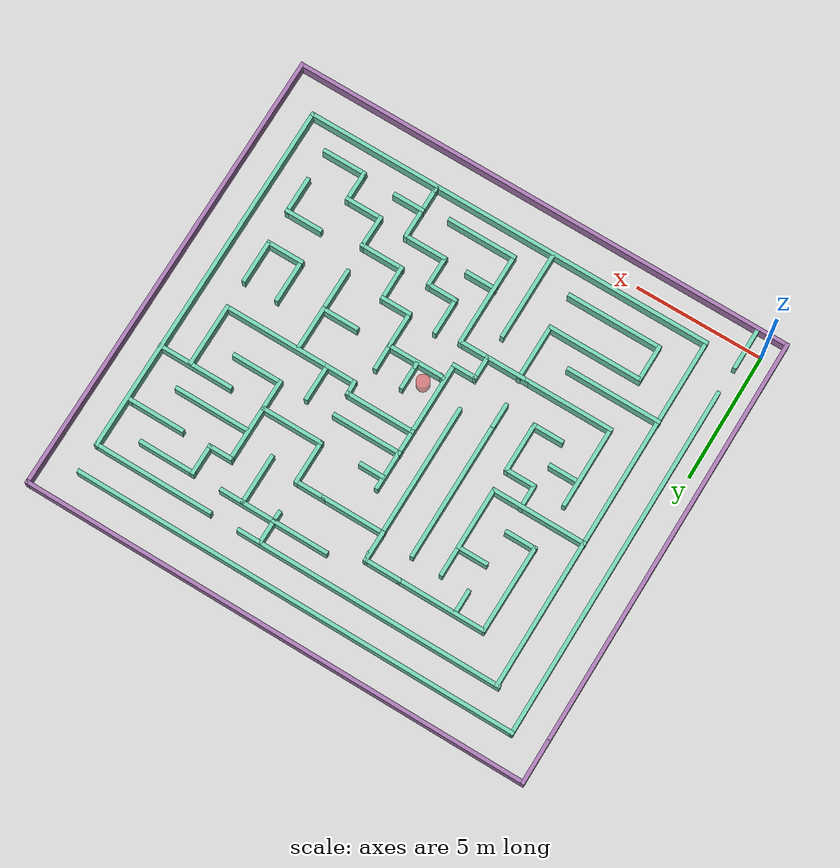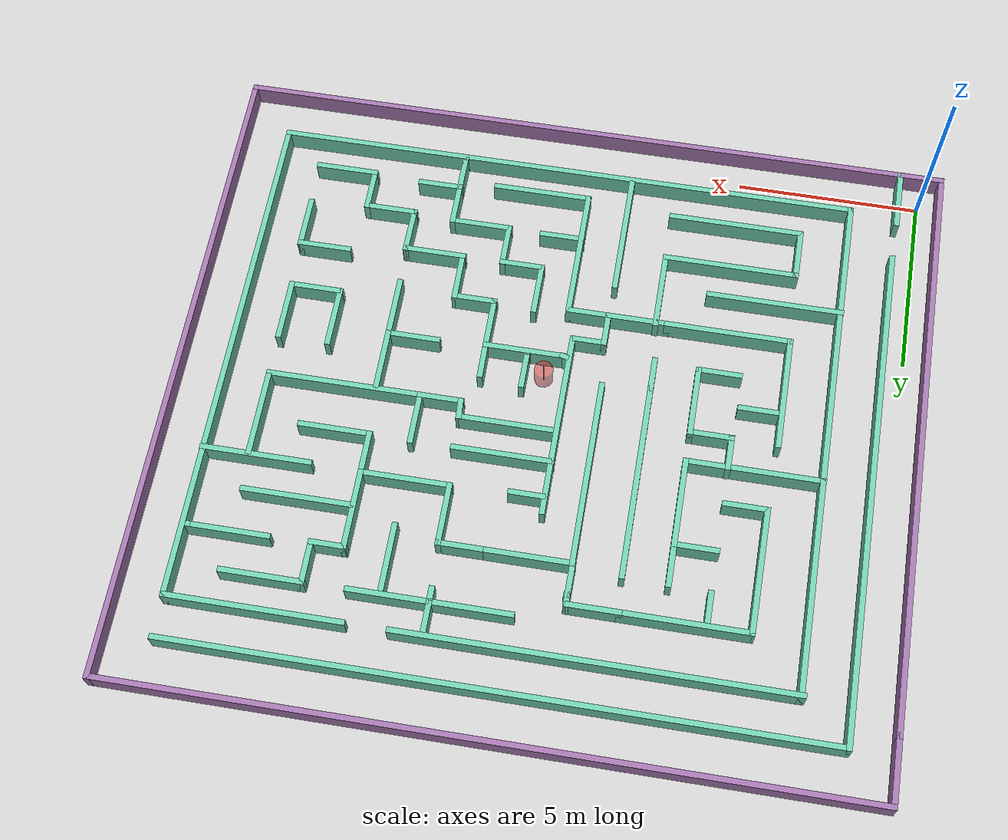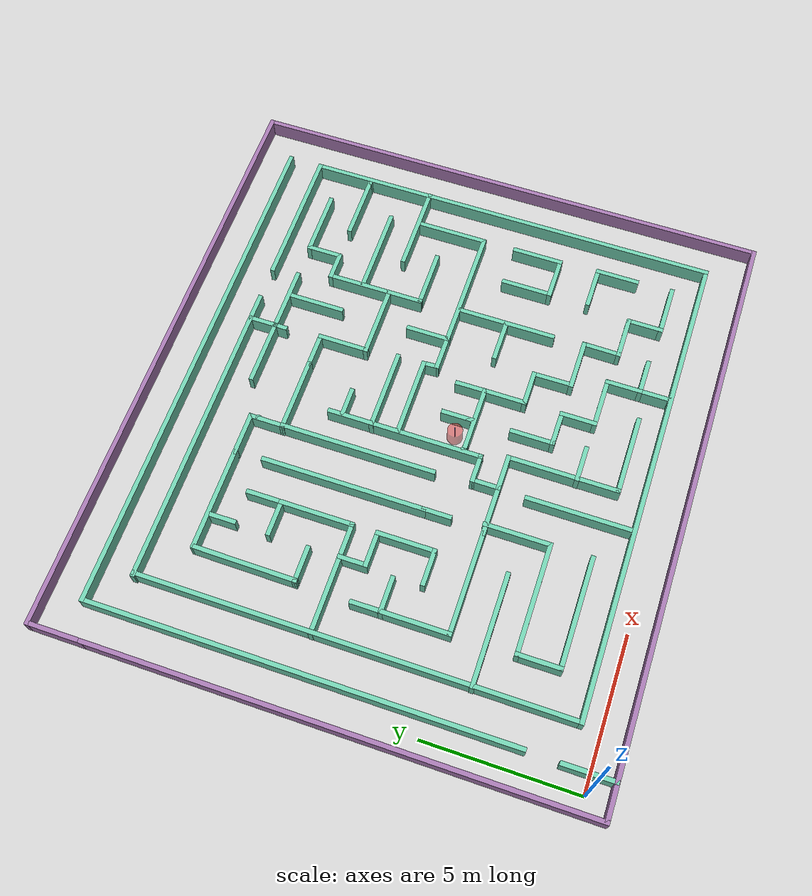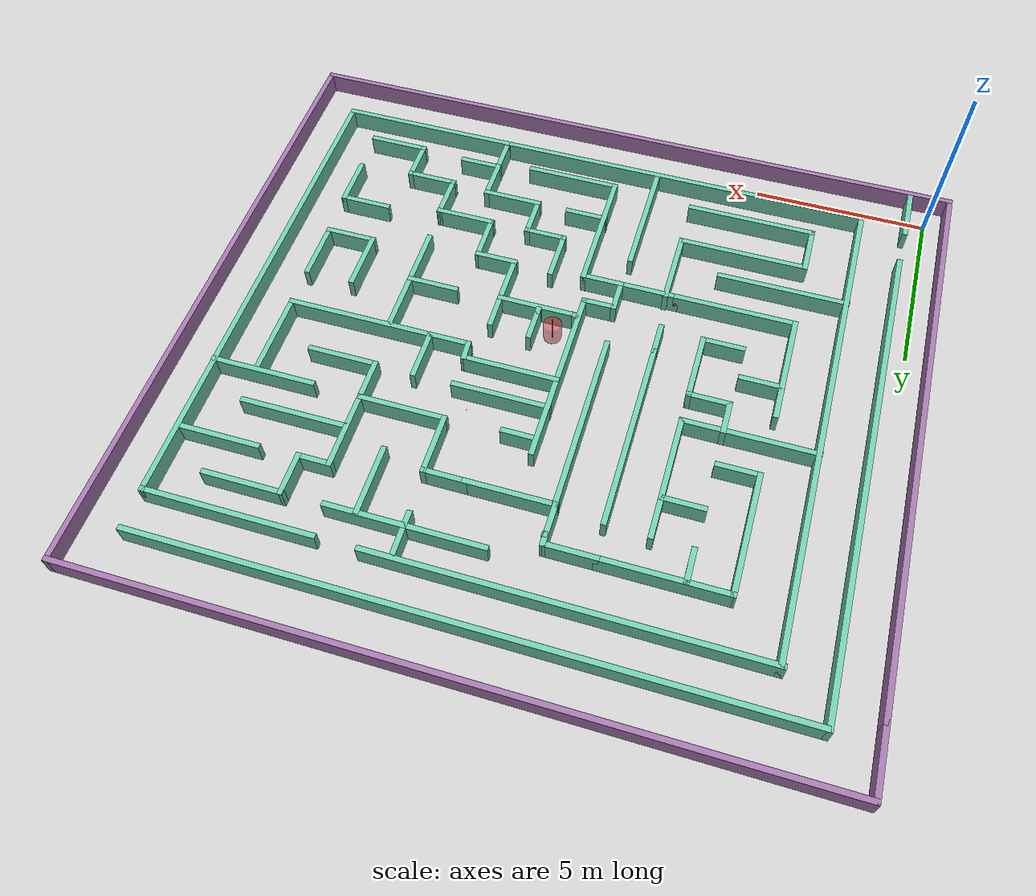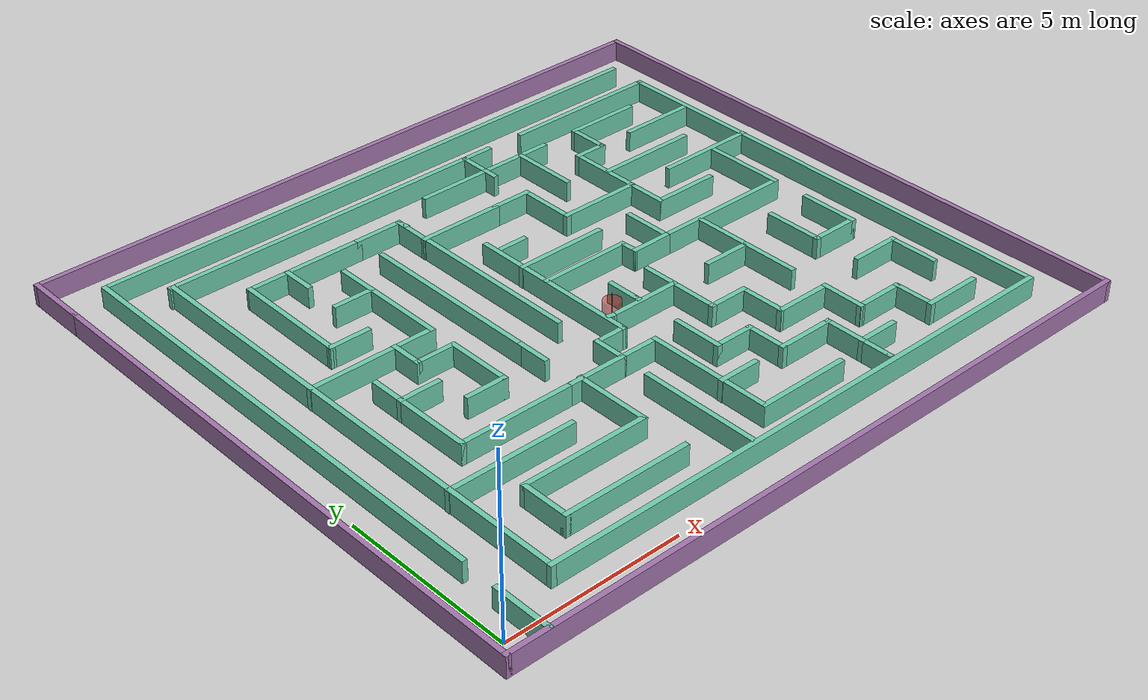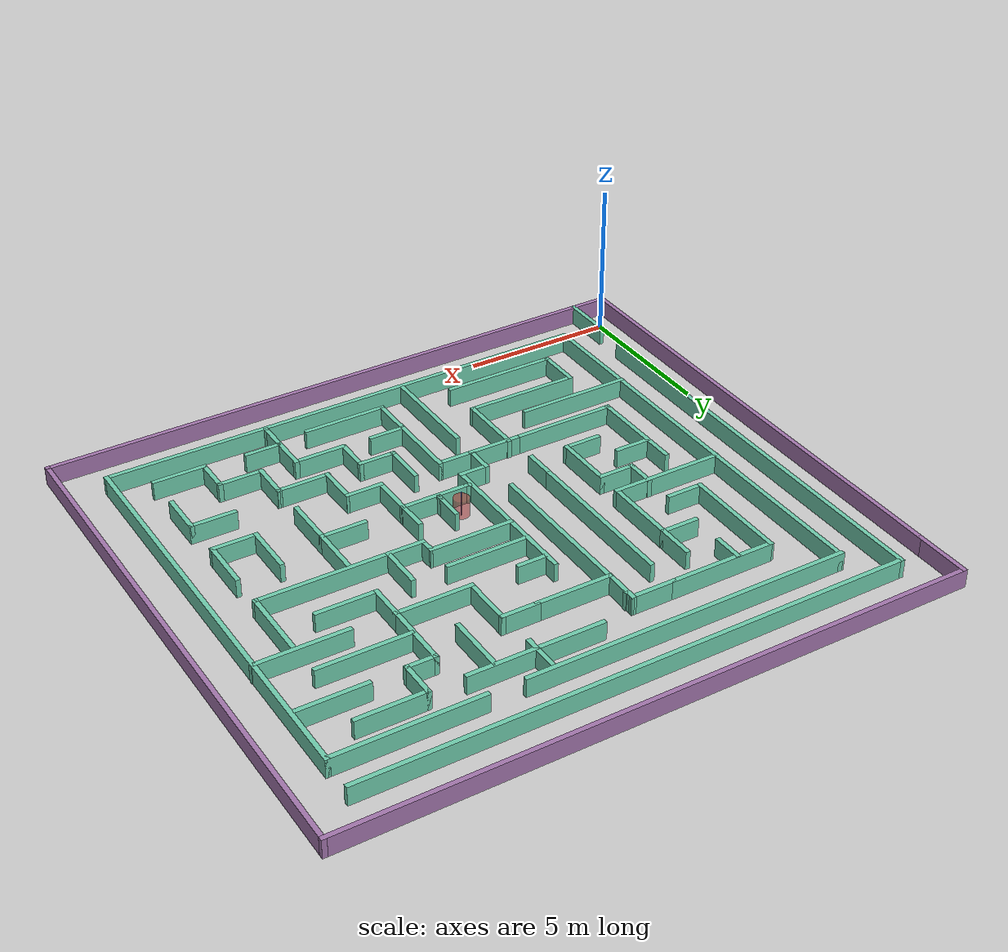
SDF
<sdf version="1.7">
 <world name="default">
  <light name="sun" type="directional">
   <pose>0 0 10 0 -0 0</pose>
   <diffuse>0.8 0.8 0.8 1</diffuse>
   <specular>0.2 0.2 0.2 1</specular>
   <attenuation>
    <range>1000</range>
    <constant>0.9</constant>
    <linear>0.01</linear>
    <quadratic>0.001</quadratic>
   </attenuation>
   <direction>-0.5 0.1 -0.9</direction>
   <spot><inner_angle>0</inner_angle><outer_angle>0</outer_angle><falloff>0</falloff></spot>
  </light>
  <model name="ground_plane">
   <static>1</static>
   <link name="link">
    <collision name="collision">
     <geometry><plane><normal>0 0 1</normal><size>100 100</size></plane></geometry>
     <surface><friction><ode><mu>100</mu><mu2>50</mu2></ode></friction></surface>
    </collision>
    <visual name="visual">
     <cast_shadows>0</cast_shadows>
     <geometry><plane><normal>0 0 1</normal><size>100 100</size></plane></geometry>
     <material>
      <script><uri>file://media/materials/scripts/gazebo.material</uri><name>Gazebo/Grey</name></script>
     </material>
    </visual>
   </link>
  </model>
  <gravity>0 0 -9.8</gravity>
  <magnetic_field>6e-06 2.3e-05 -4.2e-05</magnetic_field>
  <atmosphere type="adiabatic"/>
  <physics type="ode">
   <max_step_size>0.001</max_step_size>
   <real_time_factor>1</real_time_factor>
   <real_time_update_rate>1000</real_time_update_rate>
  </physics>
  <scene><ambient>0.4 0.4 0.4 1</ambient><background>0.7 0.7 0.7 1</background><shadows>1</shadows></scene>
  <audio><device>default</device></audio>
  <spherical_coordinates>
   <surface_model>EARTH_WGS84</surface_model>
   <latitude_deg>0</latitude_deg>
   <longitude_deg>0</longitude_deg>
   <elevation>0</elevation>
   <heading_deg>0</heading_deg>
  </spherical_coordinates>
  <model name="goal">
   <static>true</static>
   <pose>9.56186 6.95623 0.3 0 0 0</pose>
   <link name="link">
    <visual name="visual">
     <geometry><cylinder><radius>0.25</radius><length>0.6</length></cylinder></geometry>
     <material>
      <script><name>Gazebo/RedTransparent</name><uri>file://media/materials/scripts/gazebo.material</uri></script>
     </material>
    </visual>
   </link>
   <link name="link2">
    <visual name="visual2">
     <geometry><cylinder><radius>0.01</radius><length>1</length></cylinder></geometry>
     <material>
      <script><name>Gazebo/Blue</name><uri>file://media/materials/scripts/gazebo.material</uri></script>
     </material>
    </visual>
   </link>
  </model>
  <model name="complicated_maze">
   <pose>-457.073 -167.601 0 0 -0 0</pose>
   <link name="Wall_104">
    <collision name="Wall_104_Collision">
     <geometry><box><size>3.5 0.15 0.6</size></box></geometry>
     <pose>0 0 0.3 0 -0 0</pose>
    </collision>
    <visual name="Wall_104_Visual">
     <pose>0 0 0.3 0 -0 0</pose>
     <geometry><box><size>3.5 0.15 0.6</size></box></geometry>
     <material>
      <script><uri>file://media/materials/scripts/gazebo.material</uri><name>Gazebo/Grey</name></script>
      <ambient>0.435294 0.796078 0.67451 1</ambient>
      <ambient>1 1 1 1</ambient>
     </material>
     <meta><layer>0</layer></meta>
    </visual>
    <pose>461.998 180.966 0 0 -0 0</pose>
   </link>
   <link name="Wall_108">
    <collision name="Wall_108_Collision">
     <geometry><box><size>1.5 0.15 0.6</size></box></geometry>
     <pose>0 0 0.3 0 -0 0</pose>
    </collision>
    <visual name="Wall_108_Visual">
     <pose>0 0 0.3 0 -0 0</pose>
     <geometry><box><size>1.5 0.15 0.6</size></box></geometry>
     <material>
      <script><uri>file://media/materials/scripts/gazebo.material</uri><name>Gazebo/Grey</name></script>
      <ambient>0.435294 0.796078 0.67451 1</ambient>
      <ambient>1 1 1 1</ambient>
     </material>
     <meta><layer>0</layer></meta>
    </visual>
    <pose>464.348 180.966 0 0 -0 0</pose>
   </link>
   <link name="Wall_109">
    <collision name="Wall_109_Collision">
     <geometry><box><size>1.25004 0.15 0.6</size></box></geometry>
     <pose>0 0 0.3 0 -0 0</pose>
    </collision>
    <visual name="Wall_109_Visual">
     <pose>0 0 0.3 0 -0 0</pose>
     <geometry><box><size>1.25004 0.15 0.6</size></box></geometry>
     <material>
      <script><uri>file://media/materials/scripts/gazebo.material</uri><name>Gazebo/Grey</name></script>
      <ambient>0.435294 0.796078 0.67451 1</ambient>
      <ambient>1 1 1 1</ambient>
     </material>
     <meta><layer>0</layer></meta>
    </visual>
    <pose>465.02 180.416 0 0 -0 -1.57624</pose>
   </link>
   <link name="Wall_111">
    <collision name="Wall_111_Collision">
     <geometry><box><size>2.25 0.15 0.6</size></box></geometry>
     <pose>0 0 0.3 0 -0 0</pose>
    </collision>
    <visual name="Wall_111_Visual">
     <pose>0 0 0.3 0 -0 0</pose>
     <geometry><box><size>2.25 0.15 0.6</size></box></geometry>
     <material>
      <script><uri>file://media/materials/scripts/gazebo.material</uri><name>Gazebo/Grey</name></script>
      <ambient>0.435294 0.796078 0.67451 1</ambient>
      <ambient>1 1 1 1</ambient>
     </material>
     <meta><layer>0</layer></meta>
    </visual>
    <pose>467.369 181.458 0 0 -0 3.14159</pose>
   </link>
   <link name="Wall_113">
    <collision name="Wall_113_Collision">
     <geometry><box><size>5.25 0.15 0.6</size></box></geometry>
     <pose>0 0 0.3 0 -0 0</pose>
    </collision>
    <visual name="Wall_113_Visual">
     <pose>0 0 0.3 0 -0 0</pose>
     <geometry><box><size>5.25 0.15 0.6</size></box></geometry>
     <material>
      <script><uri>file://media/materials/scripts/gazebo.material</uri><name>Gazebo/Grey</name></script>
      <ambient>0.435294 0.796078 0.67451 1</ambient>
      <ambient>1 1 1 1</ambient>
     </material>
     <meta><layer>0</layer></meta>
    </visual>
    <pose>465.032 177.316 0 0 -0 -1.5708</pose>
   </link>
   <link name="Wall_115">
    <collision name="Wall_115_Collision">
     <geometry><box><size>5.5 0.15 0.6</size></box></geometry>
     <pose>0 0 0.3 0 -0 0</pose>
    </collision>
    <visual name="Wall_115_Visual">
     <pose>0 0 0.3 0 -0 0</pose>
     <geometry><box><size>5.5 0.15 0.6</size></box></geometry>
     <material>
      <script><uri>file://media/materials/scripts/gazebo.material</uri><name>Gazebo/Grey</name></script>
      <ambient>0.435294 0.796078 0.67451 1</ambient>
      <ambient>1 1 1 1</ambient>
     </material>
     <meta><layer>0</layer></meta>
    </visual>
    <pose>463.74 177.328 0 0 -0 -1.5708</pose>
   </link>
   <link name="Wall_117">
    <collision name="Wall_117_Collision">
     <geometry><box><size>1.75 0.15 0.6</size></box></geometry>
     <pose>0 0 0.3 0 -0 0</pose>
    </collision>
    <visual name="Wall_117_Visual">
     <pose>0 0 0.3 0 -0 0</pose>
     <geometry><box><size>1.75 0.15 0.6</size></box></geometry>
     <material>
      <script><uri>file://media/materials/scripts/gazebo.material</uri><name>Gazebo/Grey</name></script>
      <ambient>0.435294 0.796078 0.67451 1</ambient>
      <ambient>1 1 1 1</ambient>
     </material>
     <meta><layer>0</layer></meta>
    </visual>
    <pose>464.365 172.657 0 0 -0 0</pose>
   </link>
   <link name="Wall_118">
    <collision name="Wall_118_Collision">
     <geometry><box><size>1 0.15 0.6</size></box></geometry>
     <pose>0 0 0.3 0 -0 0</pose>
    </collision>
    <visual name="Wall_118_Visual">
     <pose>0 0 0.3 0 -0 0</pose>
     <geometry><box><size>1 0.15 0.6</size></box></geometry>
     <material>
      <script><uri>file://media/materials/scripts/gazebo.material</uri><name>Gazebo/Grey</name></script>
      <ambient>0.435294 0.796078 0.67451 1</ambient>
      <ambient>1 1 1 1</ambient>
     </material>
     <meta><layer>0</layer></meta>
    </visual>
    <pose>465.165 173.082 0 0 -0 1.5708</pose>
   </link>
   <link name="Wall_120">
    <collision name="Wall_120_Collision">
     <geometry><box><size>1 0.15 0.6</size></box></geometry>
     <pose>0 0 0.3 0 -0 0</pose>
    </collision>
    <visual name="Wall_120_Visual">
     <pose>0 0 0.3 0 -0 0</pose>
     <geometry><box><size>1 0.15 0.6</size></box></geometry>
     <material>
      <script><uri>file://media/materials/scripts/gazebo.material</uri><name>Gazebo/Grey</name></script>
      <ambient>0.435294 0.796078 0.67451 1</ambient>
      <ambient>1 1 1 1</ambient>
     </material>
     <meta><layer>0</layer></meta>
    </visual>
    <pose>463.74 174.228 0 0 -0 -1.5708</pose>
   </link>
   <link name="Wall_123">
    <collision name="Wall_123_Collision">
     <geometry><box><size>1 0.15 0.6</size></box></geometry>
     <pose>0 0 0.3 0 -0 0</pose>
    </collision>
    <visual name="Wall_123_Visual">
     <pose>0 0 0.3 0 -0 0</pose>
     <geometry><box><size>1 0.15 0.6</size></box></geometry>
     <material>
      <script><uri>file://media/materials/scripts/gazebo.material</uri><name>Gazebo/Grey</name></script>
      <ambient>0.435294 0.796078 0.67451 1</ambient>
      <ambient>1 1 1 1</ambient>
     </material>
     <meta><layer>0</layer></meta>
    </visual>
    <pose>465.59 173.507 0 0 -0 0</pose>
   </link>
   <link name="Wall_124">
    <collision name="Wall_124_Collision">
     <geometry><box><size>5.25 0.15 0.6</size></box></geometry>
     <pose>0 0 0.3 0 -0 0</pose>
    </collision>
    <visual name="Wall_124_Visual">
     <pose>0 0 0.3 0 -0 0</pose>
     <geometry><box><size>5.25 0.15 0.6</size></box></geometry>
     <material>
      <script><uri>file://media/materials/scripts/gazebo.material</uri><name>Gazebo/Grey</name></script>
      <ambient>0.435294 0.796078 0.67451 1</ambient>
      <ambient>1 1 1 1</ambient>
     </material>
     <meta><layer>0</layer></meta>
    </visual>
    <pose>466.015 176.057 0 0 -0 1.5708</pose>
   </link>
   <link name="Wall_126">
    <collision name="Wall_126_Collision">
     <geometry><box><size>1 0.15 0.6</size></box></geometry>
     <pose>0 0 0.3 0 -0 0</pose>
    </collision>
    <visual name="Wall_126_Visual">
     <pose>0 0 0.3 0 -0 0</pose>
     <geometry><box><size>1 0.15 0.6</size></box></geometry>
     <material>
      <script><uri>file://media/materials/scripts/gazebo.material</uri><name>Gazebo/Grey</name></script>
      <ambient>0.435294 0.796078 0.67451 1</ambient>
      <ambient>1 1 1 1</ambient>
     </material>
     <meta><layer>0</layer></meta>
    </visual>
    <pose>466.489 178.185 0 0 -0 0</pose>
   </link>
   <link name="Wall_130">
    <collision name="Wall_130_Collision">
     <geometry><box><size>2.75 0.15 0.6</size></box></geometry>
     <pose>0 0 0.3 0 -0 0</pose>
    </collision>
    <visual name="Wall_130_Visual">
     <pose>0 0 0.3 0 -0 0</pose>
     <geometry><box><size>2.75 0.15 0.6</size></box></geometry>
     <material>
      <script><uri>file://media/materials/scripts/gazebo.material</uri><name>Gazebo/Grey</name></script>
      <ambient>0.435294 0.796078 0.67451 1</ambient>
      <ambient>1 1 1 1</ambient>
     </material>
     <meta><layer>0</layer></meta>
    </visual>
    <pose>467.305 177.176 0 0 -0 0</pose>
   </link>
   <link name="Wall_132">
    <collision name="Wall_132_Collision">
     <geometry><box><size>2.75 0.15 0.6</size></box></geometry>
     <pose>0 0 0.3 0 -0 0</pose>
    </collision>
    <visual name="Wall_132_Visual">
     <pose>0 0 0.3 0 -0 0</pose>
     <geometry><box><size>2.75 0.15 0.6</size></box></geometry>
     <material>
      <script><uri>file://media/materials/scripts/gazebo.material</uri><name>Gazebo/Grey</name></script>
      <ambient>0.435294 0.796078 0.67451 1</ambient>
      <ambient>1 1 1 1</ambient>
     </material>
     <meta><layer>0</layer></meta>
    </visual>
    <pose>467.326 176.287 0 0 -0 0</pose>
   </link>
   <link name="Wall_136">
    <collision name="Wall_136_Collision">
     <geometry><box><size>1.25 0.15 0.6</size></box></geometry>
     <pose>0 0 0.3 0 -0 0</pose>
    </collision>
    <visual name="Wall_136_Visual">
     <pose>0 0 0.3 0 -0 0</pose>
     <geometry><box><size>1.25 0.15 0.6</size></box></geometry>
     <material>
      <script><uri>file://media/materials/scripts/gazebo.material</uri><name>Gazebo/Grey</name></script>
      <ambient>0.435294 0.796078 0.67451 1</ambient>
      <ambient>1 1 1 1</ambient>
     </material>
     <meta><layer>0</layer></meta>
    </visual>
    <pose>469.202 175.833 0 0 -0 3.14159</pose>
   </link>
   <link name="Wall_137">
    <collision name="Wall_137_Collision">
     <geometry><box><size>0.603934 0.15 0.6</size></box></geometry>
     <pose>0 0 0.3 0 -0 0</pose>
    </collision>
    <visual name="Wall_137_Visual">
     <pose>0 0 0.3 0 -0 0</pose>
     <geometry><box><size>0.603934 0.15 0.6</size></box></geometry>
     <material>
      <script><uri>file://media/materials/scripts/gazebo.material</uri><name>Gazebo/Grey</name></script>
      <ambient>0.435294 0.796078 0.67451 1</ambient>
      <ambient>1 1 1 1</ambient>
     </material>
     <meta><layer>0</layer></meta>
    </visual>
    <pose>468.639 176.06 0 0 -0 1.62768</pose>
   </link>
   <link name="Wall_139">
    <collision name="Wall_139_Collision">
     <geometry><box><size>1.75 0.15 0.6</size></box></geometry>
     <pose>0 0 0.3 0 -0 0</pose>
    </collision>
    <visual name="Wall_139_Visual">
     <pose>0 0 0.3 0 -0 0</pose>
     <geometry><box><size>1.75 0.15 0.6</size></box></geometry>
     <material>
      <script><uri>file://media/materials/scripts/gazebo.material</uri><name>Gazebo/Grey</name></script>
      <ambient>0.435294 0.796078 0.67451 1</ambient>
      <ambient>1 1 1 1</ambient>
     </material>
     <meta><layer>0</layer></meta>
    </visual>
    <pose>473.865 173.889 0 0 -0 -1.5708</pose>
   </link>
   <link name="Wall_140">
    <collision name="Wall_140_Collision">
     <geometry><box><size>1.5 0.15 0.6</size></box></geometry>
     <pose>0 0 0.3 0 -0 0</pose>
    </collision>
    <visual name="Wall_140_Visual">
     <pose>0 0 0.3 0 -0 0</pose>
     <geometry><box><size>1.5 0.15 0.6</size></box></geometry>
     <material>
      <script><uri>file://media/materials/scripts/gazebo.material</uri><name>Gazebo/Grey</name></script>
      <ambient>0.435294 0.796078 0.67451 1</ambient>
      <ambient>1 1 1 1</ambient>
     </material>
     <meta><layer>0</layer></meta>
    </visual>
    <pose>473.19 173.089 0 0 -0 3.14159</pose>
   </link>
   <link name="Wall_141">
    <collision name="Wall_141_Collision">
     <geometry><box><size>1.75 0.15 0.6</size></box></geometry>
     <pose>0 0 0.3 0 -0 0</pose>
    </collision>
    <visual name="Wall_141_Visual">
     <pose>0 0 0.3 0 -0 0</pose>
     <geometry><box><size>1.75 0.15 0.6</size></box></geometry>
     <material>
      <script><uri>file://media/materials/scripts/gazebo.material</uri><name>Gazebo/Grey</name></script>
      <ambient>0.435294 0.796078 0.67451 1</ambient>
      <ambient>1 1 1 1</ambient>
     </material>
     <meta><layer>0</layer></meta>
    </visual>
    <pose>472.515 173.889 0 0 -0 1.5708</pose>
   </link>
   <link name="Wall_143">
    <collision name="Wall_143_Collision">
     <geometry><box><size>1.5 0.15 0.6</size></box></geometry>
     <pose>0 0 0.3 0 -0 0</pose>
    </collision>
    <visual name="Wall_143_Visual">
     <pose>0 0 0.3 0 -0 0</pose>
     <geometry><box><size>1.5 0.15 0.6</size></box></geometry>
     <material>
      <script><uri>file://media/materials/scripts/gazebo.material</uri><name>Gazebo/Grey</name></script>
      <ambient>0.435294 0.796078 0.67451 1</ambient>
      <ambient>1 1 1 1</ambient>
     </material>
     <meta><layer>0</layer></meta>
    </visual>
    <pose>473.25 171.758 0 0 -0 0</pose>
   </link>
   <link name="Wall_144">
    <collision name="Wall_144_Collision">
     <geometry><box><size>1.5 0.15 0.6</size></box></geometry>
     <pose>0 0 0.3 0 -0 0</pose>
    </collision>
    <visual name="Wall_144_Visual">
     <pose>0 0 0.3 0 -0 0</pose>
     <geometry><box><size>1.5 0.15 0.6</size></box></geometry>
     <material>
      <script><uri>file://media/materials/scripts/gazebo.material</uri><name>Gazebo/Grey</name></script>
      <ambient>0.435294 0.796078 0.67451 1</ambient>
      <ambient>1 1 1 1</ambient>
     </material>
     <meta><layer>0</layer></meta>
    </visual>
    <pose>473.925 171.083 0 0 -0 -1.5708</pose>
   </link>
   <link name="Wall_147">
    <collision name="Wall_147_Collision">
     <geometry><box><size>1.75 0.15 0.6</size></box></geometry>
     <pose>0 0 0.3 0 -0 0</pose>
    </collision>
    <visual name="Wall_147_Visual">
     <pose>0 0 0.3 0 -0 0</pose>
     <geometry><box><size>1.75 0.15 0.6</size></box></geometry>
     <material>
      <script><uri>file://media/materials/scripts/gazebo.material</uri><name>Gazebo/Grey</name></script>
      <ambient>0.435294 0.796078 0.67451 1</ambient>
      <ambient>1 1 1 1</ambient>
     </material>
     <meta><layer>0</layer></meta>
    </visual>
    <pose>473.149 169.177 0 0 -0 3.14159</pose>
   </link>
   <link name="Wall_148">
    <collision name="Wall_148_Collision">
     <geometry><box><size>1.25 0.15 0.6</size></box></geometry>
     <pose>0 0 0.3 0 -0 0</pose>
    </collision>
    <visual name="Wall_148_Visual">
     <pose>0 0 0.3 0 -0 0</pose>
     <geometry><box><size>1.25 0.15 0.6</size></box></geometry>
     <material>
      <script><uri>file://media/materials/scripts/gazebo.material</uri><name>Gazebo/Grey</name></script>
      <ambient>0.435294 0.796078 0.67451 1</ambient>
      <ambient>1 1 1 1</ambient>
     </material>
     <meta><layer>0</layer></meta>
    </visual>
    <pose>472.349 169.727 0 0 -0 1.5708</pose>
   </link>
   <link name="Wall_149">
    <collision name="Wall_149_Collision">
     <geometry><box><size>1.5 0.15 0.6</size></box></geometry>
     <pose>0 0 0.3 0 -0 0</pose>
    </collision>
    <visual name="Wall_149_Visual">
     <pose>0 0 0.3 0 -0 0</pose>
     <geometry><box><size>1.5 0.15 0.6</size></box></geometry>
     <material>
      <script><uri>file://media/materials/scripts/gazebo.material</uri><name>Gazebo/Grey</name></script>
      <ambient>0.435294 0.796078 0.67451 1</ambient>
      <ambient>1 1 1 1</ambient>
     </material>
     <meta><layer>0</layer></meta>
    </visual>
    <pose>471.674 170.277 0 0 -0 3.14159</pose>
   </link>
   <link name="Wall_150">
    <collision name="Wall_150_Collision">
     <geometry><box><size>1.33389 0.15 0.6</size></box></geometry>
     <pose>0 0 0.3 0 -0 0</pose>
    </collision>
    <visual name="Wall_150_Visual">
     <pose>0 0 0.3 0 -0 0</pose>
     <geometry><box><size>1.33389 0.15 0.6</size></box></geometry>
     <material>
      <script><uri>file://media/materials/scripts/gazebo.material</uri><name>Gazebo/Grey</name></script>
      <ambient>0.435294 0.796078 0.67451 1</ambient>
      <ambient>1 1 1 1</ambient>
     </material>
     <meta><layer>0</layer></meta>
    </visual>
    <pose>471.006 170.869 0 0 -0 1.56</pose>
   </link>
   <link name="Wall_151">
    <collision name="Wall_151_Collision">
     <geometry><box><size>1.75 0.15 0.6</size></box></geometry>
     <pose>0 0 0.3 0 -0 0</pose>
    </collision>
    <visual name="Wall_151_Visual">
     <pose>0 0 0.3 0 -0 0</pose>
     <geometry><box><size>1.75 0.15 0.6</size></box></geometry>
     <material>
      <script><uri>file://media/materials/scripts/gazebo.material</uri><name>Gazebo/Grey</name></script>
      <ambient>0.435294 0.796078 0.67451 1</ambient>
      <ambient>1 1 1 1</ambient>
     </material>
     <meta><layer>0</layer></meta>
    </visual>
    <pose>470.199 171.461 0 0 -0 3.14159</pose>
   </link>
   <link name="Wall_152">
    <collision name="Wall_152_Collision">
     <geometry><box><size>1.41625 0.15 0.6</size></box></geometry>
     <pose>0 0 0.3 0 -0 0</pose>
    </collision>
    <visual name="Wall_152_Visual">
     <pose>0 0 0.3 0 -0 0</pose>
     <geometry><box><size>1.41625 0.15 0.6</size></box></geometry>
     <material>
      <script><uri>file://media/materials/scripts/gazebo.material</uri><name>Gazebo/Grey</name></script>
      <ambient>0.435294 0.796078 0.67451 1</ambient>
      <ambient>1 1 1 1</ambient>
     </material>
     <meta><layer>0</layer></meta>
    </visual>
    <pose>469.406 172.094 0 0 -0 1.58089</pose>
   </link>
   <link name="Wall_153">
    <collision name="Wall_153_Collision">
     <geometry><box><size>1.25 0.15 0.6</size></box></geometry>
     <pose>0 0 0.3 0 -0 0</pose>
    </collision>
    <visual name="Wall_153_Visual">
     <pose>0 0 0.3 0 -0 0</pose>
     <geometry><box><size>1.25 0.15 0.6</size></box></geometry>
     <material>
      <script><uri>file://media/materials/scripts/gazebo.material</uri><name>Gazebo/Grey</name></script>
      <ambient>0.435294 0.796078 0.67451 1</ambient>
      <ambient>1 1 1 1</ambient>
     </material>
     <meta><layer>0</layer></meta>
    </visual>
    <pose>468.849 172.727 0 0 -0 3.14159</pose>
   </link>
   <link name="Wall_154">
    <collision name="Wall_154_Collision">
     <geometry><box><size>1.5 0.15 0.6</size></box></geometry>
     <pose>0 0 0.3 0 -0 0</pose>
    </collision>
    <visual name="Wall_154_Visual">
     <pose>0 0 0.3 0 -0 0</pose>
     <geometry><box><size>1.5 0.15 0.6</size></box></geometry>
     <material>
      <script><uri>file://media/materials/scripts/gazebo.material</uri><name>Gazebo/Grey</name></script>
      <ambient>0.435294 0.796078 0.67451 1</ambient>
      <ambient>1 1 1 1</ambient>
     </material>
     <meta><layer>0</layer></meta>
    </visual>
    <pose>468.299 173.402 0 0 -0 1.5708</pose>
   </link>
   <link name="Wall_155">
    <collision name="Wall_155_Collision">
     <geometry><box><size>2.25 0.15 0.6</size></box></geometry>
     <pose>0 0 0.3 0 -0 0</pose>
    </collision>
    <visual name="Wall_155_Visual">
     <pose>0 0 0.3 0 -0 0</pose>
     <geometry><box><size>2.25 0.15 0.6</size></box></geometry>
     <material>
      <script><uri>file://media/materials/scripts/gazebo.material</uri><name>Gazebo/Grey</name></script>
      <ambient>0.435294 0.796078 0.67451 1</ambient>
      <ambient>1 1 1 1</ambient>
     </material>
     <meta><layer>0</layer></meta>
    </visual>
    <pose>467.249 174.077 0 0 -0 3.14159</pose>
   </link>
   <link name="Wall_156">
    <collision name="Wall_156_Collision">
     <geometry><box><size>0.25 0.15 0.6</size></box></geometry>
     <pose>0 0 0.3 0 -0 0</pose>
    </collision>
    <visual name="Wall_156_Visual">
     <pose>0 0 0.3 0 -0 0</pose>
     <geometry><box><size>0.25 0.15 0.6</size></box></geometry>
     <material>
      <script><uri>file://media/materials/scripts/gazebo.material</uri><name>Gazebo/Grey</name></script>
      <ambient>0.435294 0.796078 0.67451 1</ambient>
      <ambient>1 1 1 1</ambient>
     </material>
     <meta><layer>0</layer></meta>
    </visual>
    <pose>466.151 174.09 0 0 -0 2.87979</pose>
   </link>
   <link name="Wall_158">
    <collision name="Wall_158_Collision">
     <geometry><box><size>1.07287 0.15 0.6</size></box></geometry>
     <pose>0 0 0.3 0 -0 0</pose>
    </collision>
    <visual name="Wall_158_Visual">
     <pose>0 0 0.3 0 -0 0</pose>
     <geometry><box><size>1.07287 0.15 0.6</size></box></geometry>
     <material>
      <script><uri>file://media/materials/scripts/gazebo.material</uri><name>Gazebo/Grey</name></script>
      <ambient>0.435294 0.796078 0.67451 1</ambient>
      <ambient>1 1 1 1</ambient>
     </material>
     <meta><layer>0</layer></meta>
    </visual>
    <pose>468.294 174.539 0 0 -0 -1.55921</pose>
   </link>
   <link name="Wall_16">
    <collision name="Wall_16_Collision">
     <geometry><box><size>16.25 0.15 0.6</size></box></geometry>
     <pose>0 0 0.3 0 -0 0</pose>
    </collision>
    <visual name="Wall_16_Visual">
     <pose>0 0 0.3 0 -0 0</pose>
     <geometry><box><size>16.25 0.15 0.6</size></box></geometry>
     <material>
      <script><uri>file://media/materials/scripts/gazebo.material</uri><name>Gazebo/Grey</name></script>
      <ambient>0.635294 0.46078 0.67451 1</ambient>
     </material>
     <meta><layer>0</layer></meta>
    </visual>
    <pose>456.517 174.907 0 0 -0 -1.5708</pose>
   </link>
   <link name="Wall_160">
    <collision name="Wall_160_Collision">
     <geometry><box><size>1 0.15 0.6</size></box></geometry>
     <pose>0 0 0.3 0 -0 0</pose>
    </collision>
    <visual name="Wall_160_Visual">
     <pose>0 0 0.3 0 -0 0</pose>
     <geometry><box><size>1 0.15 0.6</size></box></geometry>
     <material>
      <script><uri>file://media/materials/scripts/gazebo.material</uri><name>Gazebo/Grey</name></script>
      <ambient>0.435294 0.796078 0.67451 1</ambient>
      <ambient>1 1 1 1</ambient>
     </material>
     <meta><layer>0</layer></meta>
    </visual>
    <pose>467.15 174.69 0 0 -0 -1.5708</pose>
   </link>
   <link name="Wall_161">
    <collision name="Wall_161_Collision">
     <geometry><box><size>0.25 0.15 0.6</size></box></geometry>
     <pose>0 0 0.3 0 -0 0</pose>
    </collision>
    <visual name="Wall_161_Visual">
     <pose>0 0 0.3 0 -0 0</pose>
     <geometry><box><size>0.25 0.15 0.6</size></box></geometry>
     <material>
      <script><uri>file://media/materials/scripts/gazebo.material</uri><name>Gazebo/Grey</name></script>
      <ambient>0.435294 0.796078 0.67451 1</ambient>
      <ambient>1 1 1 1</ambient>
     </material>
     <meta><layer>0</layer></meta>
    </visual>
    <pose>467.15 174.215 0 0 -0 -1.5708</pose>
   </link>
   <link name="Wall_163">
    <collision name="Wall_163_Collision">
     <geometry><box><size>1.5 0.15 0.6</size></box></geometry>
     <pose>0 0 0.3 0 -0 0</pose>
    </collision>
    <visual name="Wall_163_Visual">
     <pose>0 0 0.3 0 -0 0</pose>
     <geometry><box><size>1.5 0.15 0.6</size></box></geometry>
     <material>
      <script><uri>file://media/materials/scripts/gazebo.material</uri><name>Gazebo/Grey</name></script>
      <ambient>0.435294 0.796078 0.67451 1</ambient>
      <ambient>1 1 1 1</ambient>
     </material>
     <meta><layer>0</layer></meta>
    </visual>
    <pose>470.282 174.142 0 0 -0 0</pose>
   </link>
   <link name="Wall_164">
    <collision name="Wall_164_Collision">
     <geometry><box><size>1.75 0.15 0.6</size></box></geometry>
     <pose>0 0 0.3 0 -0 0</pose>
    </collision>
    <visual name="Wall_164_Visual">
     <pose>0 0 0.3 0 -0 0</pose>
     <geometry><box><size>1.75 0.15 0.6</size></box></geometry>
     <material>
      <script><uri>file://media/materials/scripts/gazebo.material</uri><name>Gazebo/Grey</name></script>
      <ambient>0.435294 0.796078 0.67451 1</ambient>
      <ambient>1 1 1 1</ambient>
     </material>
     <meta><layer>0</layer></meta>
    </visual>
    <pose>470.957 174.942 0 0 -0 1.5708</pose>
   </link>
   <link name="Wall_166">
    <collision name="Wall_166_Collision">
     <geometry><box><size>1.75 0.15 0.6</size></box></geometry>
     <pose>0 0 0.3 0 -0 0</pose>
    </collision>
    <visual name="Wall_166_Visual">
     <pose>0 0 0.3 0 -0 0</pose>
     <geometry><box><size>1.75 0.15 0.6</size></box></geometry>
     <material>
      <script><uri>file://media/materials/scripts/gazebo.material</uri><name>Gazebo/Grey</name></script>
      <ambient>0.435294 0.796078 0.67451 1</ambient>
      <ambient>1 1 1 1</ambient>
     </material>
     <meta><layer>0</layer></meta>
    </visual>
    <pose>470.957 173.342 0 0 -0 -1.5708</pose>
   </link>
   <link name="Wall_168">
    <collision name="Wall_168_Collision">
     <geometry><box><size>1.25 0.15 0.6</size></box></geometry>
     <pose>0 0 0.3 0 -0 0</pose>
    </collision>
    <visual name="Wall_168_Visual">
     <pose>0 0 0.3 0 -0 0</pose>
     <geometry><box><size>1.25 0.15 0.6</size></box></geometry>
     <material>
      <script><uri>file://media/materials/scripts/gazebo.material</uri><name>Gazebo/Grey</name></script>
      <ambient>0.435294 0.796078 0.67451 1</ambient>
      <ambient>1 1 1 1</ambient>
     </material>
     <meta><layer>0</layer></meta>
    </visual>
    <pose>470.446 169.268 0 0 -0 3.14159</pose>
   </link>
   <link name="Wall_169">
    <collision name="Wall_169_Collision">
     <geometry><box><size>1.25 0.15 0.6</size></box></geometry>
     <pose>0 0 0.3 0 -0 0</pose>
    </collision>
    <visual name="Wall_169_Visual">
     <pose>0 0 0.3 0 -0 0</pose>
     <geometry><box><size>1.25 0.15 0.6</size></box></geometry>
     <material>
      <script><uri>file://media/materials/scripts/gazebo.material</uri><name>Gazebo/Grey</name></script>
      <ambient>0.435294 0.796078 0.67451 1</ambient>
      <ambient>1 1 1 1</ambient>
     </material>
     <meta><layer>0</layer></meta>
    </visual>
    <pose>469.896 169.818 0 0 -0 1.5708</pose>
   </link>
   <link name="Wall_17">
    <collision name="Wall_17_Collision">
     <geometry><box><size>20 0.15 0.6</size></box></geometry>
     <pose>0 0 0.3 0 -0 0</pose>
    </collision>
    <visual name="Wall_17_Visual">
     <pose>0 0 0.3 0 -0 0</pose>
     <geometry><box><size>20 0.15 0.6</size></box></geometry>
     <material>
      <script><uri>file://media/materials/scripts/gazebo.material</uri><name>Gazebo/Grey</name></script>
      <ambient>0.635294 0.46078 0.67451 1</ambient>
     </material>
     <meta><layer>0</layer></meta>
    </visual>
    <pose>466.442 166.857 0 0 -0 0</pose>
   </link>
   <link name="Wall_170">
    <collision name="Wall_170_Collision">
     <geometry><box><size>1.75 0.15 0.6</size></box></geometry>
     <pose>0 0 0.3 0 -0 0</pose>
    </collision>
    <visual name="Wall_170_Visual">
     <pose>0 0 0.3 0 -0 0</pose>
     <geometry><box><size>1.75 0.15 0.6</size></box></geometry>
     <material>
      <script><uri>file://media/materials/scripts/gazebo.material</uri><name>Gazebo/Grey</name></script>
      <ambient>0.435294 0.796078 0.67451 1</ambient>
      <ambient>1 1 1 1</ambient>
     </material>
     <meta><layer>0</layer></meta>
    </visual>
    <pose>469.096 170.368 0 0 -0 3.14159</pose>
   </link>
   <link name="Wall_171">
    <collision name="Wall_171_Collision">
     <geometry><box><size>1.25 0.15 0.6</size></box></geometry>
     <pose>0 0 0.3 0 -0 0</pose>
    </collision>
    <visual name="Wall_171_Visual">
     <pose>0 0 0.3 0 -0 0</pose>
     <geometry><box><size>1.25 0.15 0.6</size></box></geometry>
     <material>
      <script><uri>file://media/materials/scripts/gazebo.material</uri><name>Gazebo/Grey</name></script>
      <ambient>0.435294 0.796078 0.67451 1</ambient>
      <ambient>1 1 1 1</ambient>
     </material>
     <meta><layer>0</layer></meta>
    </visual>
    <pose>468.296 170.918 0 0 -0 1.5708</pose>
   </link>
   <link name="Wall_172">
    <collision name="Wall_172_Collision">
     <geometry><box><size>1.25 0.15 0.6</size></box></geometry>
     <pose>0 0 0.3 0 -0 0</pose>
    </collision>
    <visual name="Wall_172_Visual">
     <pose>0 0 0.3 0 -0 0</pose>
     <geometry><box><size>1.25 0.15 0.6</size></box></geometry>
     <material>
      <script><uri>file://media/materials/scripts/gazebo.material</uri><name>Gazebo/Grey</name></script>
      <ambient>0.435294 0.796078 0.67451 1</ambient>
      <ambient>1 1 1 1</ambient>
     </material>
     <meta><layer>0</layer></meta>
    </visual>
    <pose>467.746 171.468 0 0 -0 3.14159</pose>
   </link>
   <link name="Wall_173">
    <collision name="Wall_173_Collision">
     <geometry><box><size>1.5 0.15 0.6</size></box></geometry>
     <pose>0 0 0.3 0 -0 0</pose>
    </collision>
    <visual name="Wall_173_Visual">
     <pose>0 0 0.3 0 -0 0</pose>
     <geometry><box><size>1.5 0.15 0.6</size></box></geometry>
     <material>
      <script><uri>file://media/materials/scripts/gazebo.material</uri><name>Gazebo/Grey</name></script>
      <ambient>0.435294 0.796078 0.67451 1</ambient>
      <ambient>1 1 1 1</ambient>
     </material>
     <meta><layer>0</layer></meta>
    </visual>
    <pose>467.196 172.143 0 0 -0 1.5708</pose>
   </link>
   <link name="Wall_177">
    <collision name="Wall_177_Collision">
     <geometry><box><size>1 0.15 0.6</size></box></geometry>
     <pose>0 0 0.3 0 -0 0</pose>
    </collision>
    <visual name="Wall_177_Visual">
     <pose>0 0 0.3 0 -0 0</pose>
     <geometry><box><size>1 0.15 0.6</size></box></geometry>
     <material>
      <script><uri>file://media/materials/scripts/gazebo.material</uri><name>Gazebo/Grey</name></script>
      <ambient>0.435294 0.796078 0.67451 1</ambient>
      <ambient>1 1 1 1</ambient>
     </material>
     <meta><layer>0</layer></meta>
    </visual>
    <pose>469.896 168.843 0 0 -0 -1.5708</pose>
   </link>
   <link name="Wall_178">
    <collision name="Wall_178_Collision">
     <geometry><box><size>0.25 0.15 0.6</size></box></geometry>
     <pose>0 0 0.3 0 -0 0</pose>
    </collision>
    <visual name="Wall_178_Visual">
     <pose>0 0 0.3 0 -0 0</pose>
     <geometry><box><size>0.25 0.15 0.6</size></box></geometry>
     <material>
      <script><uri>file://media/materials/scripts/gazebo.material</uri><name>Gazebo/Grey</name></script>
      <ambient>0.435294 0.796078 0.67451 1</ambient>
      <ambient>1 1 1 1</ambient>
     </material>
     <meta><layer>0</layer></meta>
    </visual>
    <pose>469.896 168.368 0 0 -0 -1.5708</pose>
   </link>
   <link name="Wall_18">
    <collision name="Wall_18_Collision">
     <geometry><box><size>18 0.15 0.6</size></box></geometry>
     <pose>0 0 0.3 0 -0 0</pose>
    </collision>
    <visual name="Wall_18_Visual">
     <pose>0 0 0.3 0 -0 0</pose>
     <geometry><box><size>18 0.15 0.6</size></box></geometry>
     <material>
      <script><uri>file://media/materials/scripts/gazebo.material</uri><name>Gazebo/Grey</name></script>
      <ambient>0.635294 0.46078 0.67451 1</ambient>
     </material>
     <meta><layer>0</layer></meta>
    </visual>
    <pose>476.367 175.782 0 0 -0 1.5708</pose>
   </link>
   <link name="Wall_182">
    <collision name="Wall_182_Collision">
     <geometry><box><size>3.5 0.15 0.6</size></box></geometry>
     <pose>0 0 0.3 0 -0 0</pose>
    </collision>
    <visual name="Wall_182_Visual">
     <pose>0 0 0.3 0 -0 0</pose>
     <geometry><box><size>3.5 0.15 0.6</size></box></geometry>
     <material>
      <script><uri>file://media/materials/scripts/gazebo.material</uri><name>Gazebo/Grey</name></script>
      <ambient>0.435294 0.796078 0.67451 1</ambient>
      <ambient>1 1 1 1</ambient>
     </material>
     <meta><layer>0</layer></meta>
    </visual>
    <pose>465.126 170.035 0 0 -0 -1.5708</pose>
   </link>
   <link name="Wall_184">
    <collision name="Wall_184_Collision">
     <geometry><box><size>1.25 0.15 0.6</size></box></geometry>
     <pose>0 0 0.3 0 -0 0</pose>
    </collision>
    <visual name="Wall_184_Visual">
     <pose>0 0 0.3 0 -0 0</pose>
     <geometry><box><size>1.25 0.15 0.6</size></box></geometry>
     <material>
      <script><uri>file://media/materials/scripts/gazebo.material</uri><name>Gazebo/Grey</name></script>
      <ambient>0.435294 0.796078 0.67451 1</ambient>
      <ambient>1 1 1 1</ambient>
     </material>
     <meta><layer>0</layer></meta>
    </visual>
    <pose>465.715 172.657 0 0 -0 0</pose>
   </link>
   <link name="Wall_185">
    <collision name="Wall_185_Collision">
     <geometry><box><size>3.75 0.15 0.6</size></box></geometry>
     <pose>0 0 0.3 0 -0 0</pose>
    </collision>
    <visual name="Wall_185_Visual">
     <pose>0 0 0.3 0 -0 0</pose>
     <geometry><box><size>3.75 0.15 0.6</size></box></geometry>
     <material>
      <script><uri>file://media/materials/scripts/gazebo.material</uri><name>Gazebo/Grey</name></script>
      <ambient>0.435294 0.796078 0.67451 1</ambient>
      <ambient>1 1 1 1</ambient>
     </material>
     <meta><layer>0</layer></meta>
    </visual>
    <pose>466.265 170.857 0 0 -0 -1.5708</pose>
   </link>
   <link name="Wall_187">
    <collision name="Wall_187_Collision">
     <geometry><box><size>1.25 0.15 0.6</size></box></geometry>
     <pose>0 0 0.3 0 -0 0</pose>
    </collision>
    <visual name="Wall_187_Visual">
     <pose>0 0 0.3 0 -0 0</pose>
     <geometry><box><size>1.25 0.15 0.6</size></box></geometry>
     <material>
      <script><uri>file://media/materials/scripts/gazebo.material</uri><name>Gazebo/Grey</name></script>
      <ambient>0.435294 0.796078 0.67451 1</ambient>
      <ambient>1 1 1 1</ambient>
     </material>
     <meta><layer>0</layer></meta>
    </visual>
    <pose>466.8 170.395 0 0 -0 0</pose>
   </link>
   <link name="Wall_189">
    <collision name="Wall_189_Collision">
     <geometry><box><size>2.75 0.15 0.6</size></box></geometry>
     <pose>0 0 0.3 0 -0 0</pose>
    </collision>
    <visual name="Wall_189_Visual">
     <pose>0 0 0.3 0 -0 0</pose>
     <geometry><box><size>2.75 0.15 0.6</size></box></geometry>
     <material>
      <script><uri>file://media/materials/scripts/gazebo.material</uri><name>Gazebo/Grey</name></script>
      <ambient>0.435294 0.796078 0.67451 1</ambient>
      <ambient>1 1 1 1</ambient>
     </material>
     <meta><layer>0</layer></meta>
    </visual>
    <pose>467.565 169.057 0 0 -0 0</pose>
   </link>
   <link name="Wall_19">
    <collision name="Wall_19_Collision">
     <geometry><box><size>20 0.15 0.6</size></box></geometry>
     <pose>0 0 0.3 0 -0 0</pose>
    </collision>
    <visual name="Wall_19_Visual">
     <pose>0 0 0.3 0 -0 0</pose>
     <geometry><box><size>20 0.15 0.6</size></box></geometry>
     <material>
      <script><uri>file://media/materials/scripts/gazebo.material</uri><name>Gazebo/Grey</name></script>
      <ambient>0.635294 0.46078 0.67451 1</ambient>
     </material>
     <meta><layer>0</layer></meta>
    </visual>
    <pose>466.442 184.707 0 0 -0 3.14159</pose>
   </link>
   <link name="Wall_193">
    <collision name="Wall_193_Collision">
     <geometry><box><size>2.25 0.15 0.6</size></box></geometry>
     <pose>0 0 0.3 0 -0 0</pose>
    </collision>
    <visual name="Wall_193_Visual">
     <pose>0 0 0.3 0 -0 0</pose>
     <geometry><box><size>2.25 0.15 0.6</size></box></geometry>
     <material>
      <script><uri>file://media/materials/scripts/gazebo.material</uri><name>Gazebo/Grey</name></script>
      <ambient>0.435294 0.796078 0.67451 1</ambient>
      <ambient>1 1 1 1</ambient>
     </material>
     <meta><layer>0</layer></meta>
    </visual>
    <pose>463.87 171.64 0 0 -0 -1.5708</pose>
   </link>
   <link name="Wall_194">
    <collision name="Wall_194_Collision">
     <geometry><box><size>3.75 0.15 0.6</size></box></geometry>
     <pose>0 0 0.3 0 -0 0</pose>
    </collision>
    <visual name="Wall_194_Visual">
     <pose>0 0 0.3 0 -0 0</pose>
     <geometry><box><size>3.75 0.15 0.6</size></box></geometry>
     <material>
      <script><uri>file://media/materials/scripts/gazebo.material</uri><name>Gazebo/Grey</name></script>
      <ambient>0.435294 0.796078 0.67451 1</ambient>
      <ambient>1 1 1 1</ambient>
     </material>
     <meta><layer>0</layer></meta>
    </visual>
    <pose>462.07 170.59 0 0 -0 3.14159</pose>
   </link>
   <link name="Wall_195">
    <collision name="Wall_195_Collision">
     <geometry><box><size>1.5 0.15 0.6</size></box></geometry>
     <pose>0 0 0.3 0 -0 0</pose>
    </collision>
    <visual name="Wall_195_Visual">
     <pose>0 0 0.3 0 -0 0</pose>
     <geometry><box><size>1.5 0.15 0.6</size></box></geometry>
     <material>
      <script><uri>file://media/materials/scripts/gazebo.material</uri><name>Gazebo/Grey</name></script>
      <ambient>0.435294 0.796078 0.67451 1</ambient>
      <ambient>1 1 1 1</ambient>
     </material>
     <meta><layer>0</layer></meta>
    </visual>
    <pose>460.27 169.915 0 0 -0 -1.5708</pose>
   </link>
   <link name="Wall_196">
    <collision name="Wall_196_Collision">
     <geometry><box><size>3.75 0.15 0.6</size></box></geometry>
     <pose>0 0 0.3 0 -0 0</pose>
    </collision>
    <visual name="Wall_196_Visual">
     <pose>0 0 0.3 0 -0 0</pose>
     <geometry><box><size>3.75 0.15 0.6</size></box></geometry>
     <material>
      <script><uri>file://media/materials/scripts/gazebo.material</uri><name>Gazebo/Grey</name></script>
      <ambient>0.435294 0.796078 0.67451 1</ambient>
      <ambient>1 1 1 1</ambient>
     </material>
     <meta><layer>0</layer></meta>
    </visual>
    <pose>462.07 169.24 0 0 -0 0</pose>
   </link>
   <link name="Wall_198">
    <collision name="Wall_198_Collision">
     <geometry><box><size>3.75 0.15 0.6</size></box></geometry>
     <pose>0 0 0.3 0 -0 0</pose>
    </collision>
    <visual name="Wall_198_Visual">
     <pose>0 0 0.3 0 -0 0</pose>
     <geometry><box><size>3.75 0.15 0.6</size></box></geometry>
     <material>
      <script><uri>file://media/materials/scripts/gazebo.material</uri><name>Gazebo/Grey</name></script>
      <ambient>0.435294 0.796078 0.67451 1</ambient>
      <ambient>1 1 1 1</ambient>
     </material>
     <meta><layer>0</layer></meta>
    </visual>
    <pose>460.744 171.552 0 0 -0 0</pose>
   </link>
   <link name="Wall_20">
    <collision name="Wall_20_Collision">
     <geometry><box><size>1.9 0.15 0.6</size></box></geometry>
     <pose>0 0 0.3 0 -0 0</pose>
    </collision>
    <visual name="Wall_20_Visual">
     <pose>0 0 0.3 0 -0 0</pose>
     <geometry><box><size>1.9 0.15 0.6</size></box></geometry>
     <material>
      <script><uri>file://media/materials/scripts/gazebo.material</uri><name>Gazebo/Grey</name></script>
      <ambient>0.635294 0.46078 0.67451 1</ambient>
     </material>
     <meta><layer>0</layer></meta>
    </visual>
    <pose>456.517 183.832 0 0 -0 -1.5708</pose>
   </link>
   <link name="Wall_22">
    <collision name="Wall_22_Collision">
     <geometry><box><size>14 0.15 0.6</size></box></geometry>
     <pose>0 0 0.3 0 -0 0</pose>
    </collision>
    <visual name="Wall_22_Visual">
     <pose>0 0 0.3 0 -0 0</pose>
     <geometry><box><size>14 0.15 0.6</size></box></geometry>
     <material>
      <script><uri>file://media/materials/scripts/gazebo.material</uri><name>Gazebo/Grey</name></script>
      <ambient>0.435294 0.796078 0.67451 1</ambient>
      <ambient>1 1 1 1</ambient>
     </material>
     <meta><layer>0</layer></meta>
    </visual>
    <pose>457.697 176.54 0 0 -0 1.5708</pose>
   </link>
   <link name="Wall_23">
    <collision name="Wall_23_Collision">
     <geometry><box><size>17.5 0.15 0.6</size></box></geometry>
     <pose>0 0 0.3 0 -0 0</pose>
    </collision>
    <visual name="Wall_23_Visual">
     <pose>0 0 0.3 0 -0 0</pose>
     <geometry><box><size>17.5 0.15 0.6</size></box></geometry>
     <material>
      <script><uri>file://media/materials/scripts/gazebo.material</uri><name>Gazebo/Grey</name></script>
      <ambient>0.435294 0.796078 0.67451 1</ambient>
      <ambient>1 1 1 1</ambient>
     </material>
     <meta><layer>0</layer></meta>
    </visual>
    <pose>466.372 183.465 0 0 -0 0</pose>
   </link>
   <link name="Wall_25">
    <collision name="Wall_25_Collision">
     <geometry><box><size>1.75 0.15 0.6</size></box></geometry>
     <pose>0 0 0.3 0 -0 0</pose>
    </collision>
    <visual name="Wall_25_Visual">
     <pose>0 0 0.3 0 -0 0</pose>
     <geometry><box><size>1.75 0.15 0.6</size></box></geometry>
     <material>
      <script><uri>file://media/materials/scripts/gazebo.material</uri><name>Gazebo/Grey</name></script>
      <ambient>0.435294 0.796078 0.67451 1</ambient>
      <ambient>1 1 1 1</ambient>
     </material>
     <meta><layer>0</layer></meta>
    </visual>
    <pose>457.663 167.674 0 0 -0 -1.5708</pose>
   </link>
   <link name="Wall_27">
    <collision name="Wall_27_Collision">
     <geometry><box><size>10.5 0.15 0.6</size></box></geometry>
     <pose>0 0 0.3 0 -0 0</pose>
    </collision>
    <visual name="Wall_27_Visual">
     <pose>0 0 0.3 0 -0 0</pose>
     <geometry><box><size>10.5 0.15 0.6</size></box></geometry>
     <material>
      <script><uri>file://media/materials/scripts/gazebo.material</uri><name>Gazebo/Grey</name></script>
      <ambient>0.435294 0.796078 0.67451 1</ambient>
      <ambient>1 1 1 1</ambient>
     </material>
     <meta><layer>0</layer></meta>
    </visual>
    <pose>464.083 182.343 0 0 -0 0</pose>
   </link>
   <link name="Wall_29">
    <collision name="Wall_29_Collision">
     <geometry><box><size>4.75 0.15 0.6</size></box></geometry>
     <pose>0 0 0.3 0 -0 0</pose>
    </collision>
    <visual name="Wall_29_Visual">
     <pose>0 0 0.3 0 -0 0</pose>
     <geometry><box><size>4.75 0.15 0.6</size></box></geometry>
     <material>
      <script><uri>file://media/materials/scripts/gazebo.material</uri><name>Gazebo/Grey</name></script>
      <ambient>0.435294 0.796078 0.67451 1</ambient>
      <ambient>1 1 1 1</ambient>
     </material>
     <meta><layer>0</layer></meta>
    </visual>
    <pose>472.76 182.343 0 0 -0 0</pose>
   </link>
   <link name="Wall_30">
    <collision name="Wall_30_Collision">
     <geometry><box><size>14.25 0.15 0.6</size></box></geometry>
     <pose>0 0 0.3 0 -0 0</pose>
    </collision>
    <visual name="Wall_30_Visual">
     <pose>0 0 0.3 0 -0 0</pose>
     <geometry><box><size>14.25 0.15 0.6</size></box></geometry>
     <material>
      <script><uri>file://media/materials/scripts/gazebo.material</uri><name>Gazebo/Grey</name></script>
      <ambient>0.435294 0.796078 0.67451 1</ambient>
      <ambient>1 1 1 1</ambient>
     </material>
     <meta><layer>0</layer></meta>
    </visual>
    <pose>475.06 175.293 0 0 -0 -1.5708</pose>
   </link>
   <link name="Wall_31">
    <collision name="Wall_31_Collision">
     <geometry><box><size>16.25 0.15 0.6</size></box></geometry>
     <pose>0 0 0.3 0 -0 0</pose>
    </collision>
    <visual name="Wall_31_Visual">
     <pose>0 0 0.3 0 -0 0</pose>
     <geometry><box><size>16.25 0.15 0.6</size></box></geometry>
     <material>
      <script><uri>file://media/materials/scripts/gazebo.material</uri><name>Gazebo/Grey</name></script>
      <ambient>0.435294 0.796078 0.67451 1</ambient>
      <ambient>1 1 1 1</ambient>
     </material>
     <meta><layer>0</layer></meta>
    </visual>
    <pose>467.01 168.243 0 0 -0 3.14159</pose>
   </link>
   <link name="Wall_32">
    <collision name="Wall_32_Collision">
     <geometry><box><size>14.25 0.15 0.6</size></box></geometry>
     <pose>0 0 0.3 0 -0 0</pose>
    </collision>
    <visual name="Wall_32_Visual">
     <pose>0 0 0.3 0 -0 0</pose>
     <geometry><box><size>14.25 0.15 0.6</size></box></geometry>
     <material>
      <script><uri>file://media/materials/scripts/gazebo.material</uri><name>Gazebo/Grey</name></script>
      <ambient>0.435294 0.796078 0.67451 1</ambient>
      <ambient>1 1 1 1</ambient>
     </material>
     <meta><layer>0</layer></meta>
    </visual>
    <pose>458.96 175.293 0 0 -0 1.5708</pose>
   </link>
   <link name="Wall_34">
    <collision name="Wall_34_Collision">
     <geometry><box><size>1 0.15 0.6</size></box></geometry>
     <pose>0 0 0.3 0 -0 0</pose>
    </collision>
    <visual name="Wall_34_Visual">
     <pose>0 0 0.3 0 -0 0</pose>
     <geometry><box><size>1 0.15 0.6</size></box></geometry>
     <material>
      <script><uri>file://media/materials/scripts/gazebo.material</uri><name>Gazebo/Grey</name></script>
      <ambient>0.435294 0.796078 0.67451 1</ambient>
      <ambient>1 1 1 1</ambient>
     </material>
     <meta><layer>0</layer></meta>
    </visual>
    <pose>468.419 181.883 0 0 -0 -1.5708</pose>
   </link>
   <link name="Wall_35">
    <collision name="Wall_35_Collision">
     <geometry><box><size>2.25 0.15 0.6</size></box></geometry>
     <pose>0 0 0.3 0 -0 0</pose>
    </collision>
    <visual name="Wall_35_Visual">
     <pose>0 0 0.3 0 -0 0</pose>
     <geometry><box><size>2.25 0.15 0.6</size></box></geometry>
     <material>
      <script><uri>file://media/materials/scripts/gazebo.material</uri><name>Gazebo/Grey</name></script>
      <ambient>0.435294 0.796078 0.67451 1</ambient>
      <ambient>1 1 1 1</ambient>
     </material>
     <meta><layer>0</layer></meta>
    </visual>
    <pose>469.469 181.458 0 0 -0 0</pose>
   </link>
   <link name="Wall_37">
    <collision name="Wall_37_Collision">
     <geometry><box><size>0.5 0.15 0.6</size></box></geometry>
     <pose>0 0 0.3 0 -0 0</pose>
    </collision>
    <visual name="Wall_37_Visual">
     <pose>0 0 0.3 0 -0 0</pose>
     <geometry><box><size>0.5 0.15 0.6</size></box></geometry>
     <material>
      <script><uri>file://media/materials/scripts/gazebo.material</uri><name>Gazebo/Grey</name></script>
      <ambient>0.435294 0.796078 0.67451 1</ambient>
      <ambient>1 1 1 1</ambient>
     </material>
     <meta><layer>0</layer></meta>
    </visual>
    <pose>468.419 181.283 0 0 -0 -1.5708</pose>
   </link>
   <link name="Wall_39">
    <collision name="Wall_39_Collision">
     <geometry><box><size>2 0.15 0.6</size></box></geometry>
     <pose>0 0 0.3 0 -0 0</pose>
    </collision>
    <visual name="Wall_39_Visual">
     <pose>0 0 0.3 0 -0 0</pose>
     <geometry><box><size>2 0.15 0.6</size></box></geometry>
     <material>
      <script><uri>file://media/materials/scripts/gazebo.material</uri><name>Gazebo/Grey</name></script>
      <ambient>0.435294 0.796078 0.67451 1</ambient>
      <ambient>1 1 1 1</ambient>
     </material>
     <meta><layer>0</layer></meta>
    </visual>
    <pose>469.68 180.501 0 0 -0 -1.5708</pose>
   </link>
   <link name="Wall_41">
    <collision name="Wall_41_Collision">
     <geometry><box><size>2.25 0.15 0.6</size></box></geometry>
     <pose>0 0 0.3 0 -0 0</pose>
    </collision>
    <visual name="Wall_41_Visual">
     <pose>0 0 0.3 0 -0 0</pose>
     <geometry><box><size>2.25 0.15 0.6</size></box></geometry>
     <material>
      <script><uri>file://media/materials/scripts/gazebo.material</uri><name>Gazebo/Grey</name></script>
      <ambient>0.435294 0.796078 0.67451 1</ambient>
      <ambient>1 1 1 1</ambient>
     </material>
     <meta><layer>0</layer></meta>
    </visual>
    <pose>472.747 181.466 0 0 -0 0</pose>
   </link>
   <link name="Wall_45">
    <collision name="Wall_45_Collision">
     <geometry><box><size>1.25 0.15 0.6</size></box></geometry>
     <pose>0 0 0.3 0 -0 0</pose>
    </collision>
    <visual name="Wall_45_Visual">
     <pose>0 0 0.3 0 -0 0</pose>
     <geometry><box><size>1.25 0.15 0.6</size></box></geometry>
     <material>
      <script><uri>file://media/materials/scripts/gazebo.material</uri><name>Gazebo/Grey</name></script>
      <ambient>0.435294 0.796078 0.67451 1</ambient>
      <ambient>1 1 1 1</ambient>
     </material>
     <meta><layer>0</layer></meta>
    </visual>
    <pose>471.697 180.916 0 0 -0 -1.5708</pose>
   </link>
   <link name="Wall_46">
    <collision name="Wall_46_Collision">
     <geometry><box><size>1 0.15 0.6</size></box></geometry>
     <pose>0 0 0.3 0 -0 0</pose>
    </collision>
    <visual name="Wall_46_Visual">
     <pose>0 0 0.3 0 -0 0</pose>
     <geometry><box><size>1 0.15 0.6</size></box></geometry>
     <material>
      <script><uri>file://media/materials/scripts/gazebo.material</uri><name>Gazebo/Grey</name></script>
      <ambient>0.435294 0.796078 0.67451 1</ambient>
      <ambient>1 1 1 1</ambient>
     </material>
     <meta><layer>0</layer></meta>
    </visual>
    <pose>471.272 180.366 0 0 -0 3.14159</pose>
   </link>
   <link name="Wall_47">
    <collision name="Wall_47_Collision">
     <geometry><box><size>2.25 0.15 0.6</size></box></geometry>
     <pose>0 0 0.3 0 -0 0</pose>
    </collision>
    <visual name="Wall_47_Visual">
     <pose>0 0 0.3 0 -0 0</pose>
     <geometry><box><size>2.25 0.15 0.6</size></box></geometry>
     <material>
      <script><uri>file://media/materials/scripts/gazebo.material</uri><name>Gazebo/Grey</name></script>
      <ambient>0.435294 0.796078 0.67451 1</ambient>
      <ambient>1 1 1 1</ambient>
     </material>
     <meta><layer>0</layer></meta>
    </visual>
    <pose>470.847 179.316 0 0 -0 -1.5708</pose>
   </link>
   <link name="Wall_48">
    <collision name="Wall_48_Collision">
     <geometry><box><size>2.5 0.15 0.6</size></box></geometry>
     <pose>0 0 0.3 0 -0 0</pose>
    </collision>
    <visual name="Wall_48_Visual">
     <pose>0 0 0.3 0 -0 0</pose>
     <geometry><box><size>2.5 0.15 0.6</size></box></geometry>
     <material>
      <script><uri>file://media/materials/scripts/gazebo.material</uri><name>Gazebo/Grey</name></script>
      <ambient>0.435294 0.796078 0.67451 1</ambient>
      <ambient>1 1 1 1</ambient>
     </material>
     <meta><layer>0</layer></meta>
    </visual>
    <pose>469.672 178.266 0 0 -0 3.14159</pose>
   </link>
   <link name="Wall_49">
    <collision name="Wall_49_Collision">
     <geometry><box><size>1.75 0.15 0.6</size></box></geometry>
     <pose>0 0 0.3 0 -0 0</pose>
    </collision>
    <visual name="Wall_49_Visual">
     <pose>0 0 0.3 0 -0 0</pose>
     <geometry><box><size>1.75 0.15 0.6</size></box></geometry>
     <material>
      <script><uri>file://media/materials/scripts/gazebo.material</uri><name>Gazebo/Grey</name></script>
      <ambient>0.435294 0.796078 0.67451 1</ambient>
      <ambient>1 1 1 1</ambient>
     </material>
     <meta><layer>0</layer></meta>
    </visual>
    <pose>468.497 179.066 0 0 -0 1.5708</pose>
   </link>
   <link name="Wall_50">
    <collision name="Wall_50_Collision">
     <geometry><box><size>1.25 0.15 0.6</size></box></geometry>
     <pose>0 0 0.3 0 -0 0</pose>
    </collision>
    <visual name="Wall_50_Visual">
     <pose>0 0 0.3 0 -0 0</pose>
     <geometry><box><size>1.25 0.15 0.6</size></box></geometry>
     <material>
      <script><uri>file://media/materials/scripts/gazebo.material</uri><name>Gazebo/Grey</name></script>
      <ambient>0.435294 0.796078 0.67451 1</ambient>
      <ambient>1 1 1 1</ambient>
     </material>
     <meta><layer>0</layer></meta>
    </visual>
    <pose>467.947 179.866 0 0 -0 3.14159</pose>
   </link>
   <link name="Wall_54">
    <collision name="Wall_54_Collision">
     <geometry><box><size>2.25 0.15 0.6</size></box></geometry>
     <pose>0 0 0.3 0 -0 0</pose>
    </collision>
    <visual name="Wall_54_Visual">
     <pose>0 0 0.3 0 -0 0</pose>
     <geometry><box><size>2.25 0.15 0.6</size></box></geometry>
     <material>
      <script><uri>file://media/materials/scripts/gazebo.material</uri><name>Gazebo/Grey</name></script>
      <ambient>0.435294 0.796078 0.67451 1</ambient>
      <ambient>1 1 1 1</ambient>
     </material>
     <meta><layer>0</layer></meta>
    </visual>
    <pose>473.874 180.398 0 0 -0 0</pose>
   </link>
   <link name="Wall_55">
    <collision name="Wall_55_Collision">
     <geometry><box><size>0.15 0.15 0.6</size></box></geometry>
     <pose>0 0 0.3 0 -0 0</pose>
    </collision>
    <visual name="Wall_55_Visual">
     <pose>0 0 0.3 0 -0 0</pose>
     <geometry><box><size>0.15 0.15 0.6</size></box></geometry>
     <material>
      <script><uri>file://media/materials/scripts/gazebo.material</uri><name>Gazebo/Grey</name></script>
      <ambient>0.435294 0.796078 0.67451 1</ambient>
      <ambient>1 1 1 1</ambient>
     </material>
     <meta><layer>0</layer></meta>
    </visual>
    <pose>474.924 180.398 0 0 -0 0</pose>
   </link>
   <link name="Wall_57">
    <collision name="Wall_57_Collision">
     <geometry><box><size>3 0.15 0.6</size></box></geometry>
     <pose>0 0 0.3 0 -0 0</pose>
    </collision>
    <visual name="Wall_57_Visual">
     <pose>0 0 0.3 0 -0 0</pose>
     <geometry><box><size>3 0.15 0.6</size></box></geometry>
     <material>
      <script><uri>file://media/materials/scripts/gazebo.material</uri><name>Gazebo/Grey</name></script>
      <ambient>0.435294 0.796078 0.67451 1</ambient>
      <ambient>1 1 1 1</ambient>
     </material>
     <meta><layer>0</layer></meta>
    </visual>
    <pose>472.331 179.212 0 0 -0 0</pose>
   </link>
   <link name="Wall_59">
    <collision name="Wall_59_Collision">
     <geometry><box><size>3 0.15 0.6</size></box></geometry>
     <pose>0 0 0.3 0 -0 0</pose>
    </collision>
    <visual name="Wall_59_Visual">
     <pose>0 0 0.3 0 -0 0</pose>
     <geometry><box><size>3 0.15 0.6</size></box></geometry>
     <material>
      <script><uri>file://media/materials/scripts/gazebo.material</uri><name>Gazebo/Grey</name></script>
      <ambient>0.435294 0.796078 0.67451 1</ambient>
      <ambient>1 1 1 1</ambient>
     </material>
     <meta><layer>0</layer></meta>
    </visual>
    <pose>473.653 178.223 0 0 -0 3.14159</pose>
   </link>
   <link name="Wall_6">
    <collision name="Wall_6_Collision">
     <geometry><box><size>753.25 0.15 0.6</size></box></geometry>
     <pose>0 0 0.3 0 -0 0</pose>
    </collision>
    <visual name="Wall_6_Visual">
     <pose>0 0 0.3 0 -0 0</pose>
     <geometry><box><size>753.25 0.15 0.6</size></box></geometry>
     <material>
      <script><uri>file://media/materials/scripts/gazebo.material</uri><name>Gazebo/Grey</name></script>
      <ambient>0.435294 0.796078 0.67451 1</ambient>
      <ambient>1 1 1 1</ambient>
     </material>
     <meta><layer>0</layer></meta>
    </visual>
    <pose>-476.336 0.015564 0 0 -0 -1.5708</pose>
   </link>
   <link name="Wall_61">
    <collision name="Wall_61_Collision">
     <geometry><box><size>1.25 0.15 0.6</size></box></geometry>
     <pose>0 0 0.3 0 -0 0</pose>
    </collision>
    <visual name="Wall_61_Visual">
     <pose>0 0 0.3 0 -0 0</pose>
     <geometry><box><size>1.25 0.15 0.6</size></box></geometry>
     <material>
      <script><uri>file://media/materials/scripts/gazebo.material</uri><name>Gazebo/Grey</name></script>
      <ambient>0.435294 0.796078 0.67451 1</ambient>
      <ambient>1 1 1 1</ambient>
     </material>
     <meta><layer>0</layer></meta>
    </visual>
    <pose>470.847 177.716 0 0 -0 -1.5708</pose>
   </link>
   <link name="Wall_62">
    <collision name="Wall_62_Collision">
     <geometry><box><size>2 0.15 0.6</size></box></geometry>
     <pose>0 0 0.3 0 -0 0</pose>
    </collision>
    <visual name="Wall_62_Visual">
     <pose>0 0 0.3 0 -0 0</pose>
     <geometry><box><size>2 0.15 0.6</size></box></geometry>
     <material>
      <script><uri>file://media/materials/scripts/gazebo.material</uri><name>Gazebo/Grey</name></script>
      <ambient>0.435294 0.796078 0.67451 1</ambient>
      <ambient>1 1 1 1</ambient>
     </material>
     <meta><layer>0</layer></meta>
    </visual>
    <pose>471.772 177.166 0 0 -0 0</pose>
   </link>
   <link name="Wall_64">
    <collision name="Wall_64_Collision">
     <geometry><box><size>2.5 0.15 0.6</size></box></geometry>
     <pose>0 0 0.3 0 -0 0</pose>
    </collision>
    <visual name="Wall_64_Visual">
     <pose>0 0 0.3 0 -0 0</pose>
     <geometry><box><size>2.5 0.15 0.6</size></box></geometry>
     <material>
      <script><uri>file://media/materials/scripts/gazebo.material</uri><name>Gazebo/Grey</name></script>
      <ambient>0.435294 0.796078 0.67451 1</ambient>
      <ambient>1 1 1 1</ambient>
     </material>
     <meta><layer>0</layer></meta>
    </visual>
    <pose>473.852 177.008 0 0 -0 -1.5708</pose>
   </link>
   <link name="Wall_65">
    <collision name="Wall_65_Collision">
     <geometry><box><size>4.25 0.15 0.6</size></box></geometry>
     <pose>0 0 0.3 0 -0 0</pose>
    </collision>
    <visual name="Wall_65_Visual">
     <pose>0 0 0.3 0 -0 0</pose>
     <geometry><box><size>4.25 0.15 0.6</size></box></geometry>
     <material>
      <script><uri>file://media/materials/scripts/gazebo.material</uri><name>Gazebo/Grey</name></script>
      <ambient>0.435294 0.796078 0.67451 1</ambient>
      <ambient>1 1 1 1</ambient>
     </material>
     <meta><layer>0</layer></meta>
    </visual>
    <pose>471.802 175.833 0 0 -0 3.14159</pose>
   </link>
   <link name="Wall_66">
    <collision name="Wall_66_Collision">
     <geometry><box><size>1.5 0.15 0.6</size></box></geometry>
     <pose>0 0 0.3 0 -0 0</pose>
    </collision>
    <visual name="Wall_66_Visual">
     <pose>0 0 0.3 0 -0 0</pose>
     <geometry><box><size>1.5 0.15 0.6</size></box></geometry>
     <material>
      <script><uri>file://media/materials/scripts/gazebo.material</uri><name>Gazebo/Grey</name></script>
      <ambient>0.435294 0.796078 0.67451 1</ambient>
      <ambient>1 1 1 1</ambient>
     </material>
     <meta><layer>0</layer></meta>
    </visual>
    <pose>469.752 176.508 0 0 -0 1.5708</pose>
   </link>
   <link name="Wall_68">
    <collision name="Wall_68_Collision">
     <geometry><box><size>3.5 0.15 0.6</size></box></geometry>
     <pose>0 0 0.3 0 -0 0</pose>
    </collision>
    <visual name="Wall_68_Visual">
     <pose>0 0 0.3 0 -0 0</pose>
     <geometry><box><size>3.5 0.15 0.6</size></box></geometry>
     <material>
      <script><uri>file://media/materials/scripts/gazebo.material</uri><name>Gazebo/Grey</name></script>
      <ambient>0.435294 0.796078 0.67451 1</ambient>
      <ambient>1 1 1 1</ambient>
     </material>
     <meta><layer>0</layer></meta>
    </visual>
    <pose>460.31 179.291 0 0 -0 -1.57856</pose>
   </link>
   <link name="Wall_69">
    <collision name="Wall_69_Collision">
     <geometry><box><size>1.25 0.15 0.6</size></box></geometry>
     <pose>0 0 0.3 0 -0 0</pose>
    </collision>
    <visual name="Wall_69_Visual">
     <pose>0 0 0.3 0 -0 0</pose>
     <geometry><box><size>1.25 0.15 0.6</size></box></geometry>
     <material>
      <script><uri>file://media/materials/scripts/gazebo.material</uri><name>Gazebo/Grey</name></script>
      <ambient>0.435294 0.796078 0.67451 1</ambient>
      <ambient>1 1 1 1</ambient>
     </material>
     <meta><layer>0</layer></meta>
    </visual>
    <pose>460.847 177.616 0 0 -0 0</pose>
   </link>
   <link name="Wall_7">
    <collision name="Wall_7_Collision">
     <geometry><box><size>969.5 0.15 0.6</size></box></geometry>
     <pose>0 0 0.3 0 -0 0</pose>
    </collision>
    <visual name="Wall_7_Visual">
     <pose>0 0 0.3 0 -0 0</pose>
     <geometry><box><size>969.5 0.15 0.6</size></box></geometry>
     <material>
      <script><uri>file://media/materials/scripts/gazebo.material</uri><name>Gazebo/Grey</name></script>
      <ambient>0.435294 0.796078 0.67451 1</ambient>
      <ambient>1 1 1 1</ambient>
     </material>
     <meta><layer>0</layer></meta>
    </visual>
    <pose>-133.619 -33.8174 0 0 -0 0.785398</pose>
   </link>
   <link name="Wall_76">
    <collision name="Wall_76_Collision">
     <geometry><box><size>1 0.15 0.6</size></box></geometry>
     <pose>0 0 0.3 0 -0 0</pose>
    </collision>
    <visual name="Wall_76_Visual">
     <pose>0 0 0.3 0 -0 0</pose>
     <geometry><box><size>1 0.15 0.6</size></box></geometry>
     <material>
      <script><uri>file://media/materials/scripts/gazebo.material</uri><name>Gazebo/Grey</name></script>
      <ambient>0.435294 0.796078 0.67451 1</ambient>
      <ambient>1 1 1 1</ambient>
     </material>
     <meta><layer>0</layer></meta>
    </visual>
    <pose>461.462 180.516 0 0 -0 -1.5708</pose>
   </link>
   <link name="Wall_78">
    <collision name="Wall_78_Collision">
     <geometry><box><size>1.25 0.15 0.6</size></box></geometry>
     <pose>0 0 0.3 0 -0 0</pose>
    </collision>
    <visual name="Wall_78_Visual">
     <pose>0 0 0.3 0 -0 0</pose>
     <geometry><box><size>1.25 0.15 0.6</size></box></geometry>
     <material>
      <script><uri>file://media/materials/scripts/gazebo.material</uri><name>Gazebo/Grey</name></script>
      <ambient>0.435294 0.796078 0.67451 1</ambient>
      <ambient>1 1 1 1</ambient>
     </material>
     <meta><layer>0</layer></meta>
    </visual>
    <pose>461.999 178.938 0 0 -0 0</pose>
   </link>
   <link name="Wall_79">
    <collision name="Wall_79_Collision">
     <geometry><box><size>1.25 0.15 0.6</size></box></geometry>
     <pose>0 0 0.3 0 -0 0</pose>
    </collision>
    <visual name="Wall_79_Visual">
     <pose>0 0 0.3 0 -0 0</pose>
     <geometry><box><size>1.25 0.15 0.6</size></box></geometry>
     <material>
      <script><uri>file://media/materials/scripts/gazebo.material</uri><name>Gazebo/Grey</name></script>
      <ambient>0.435294 0.796078 0.67451 1</ambient>
      <ambient>1 1 1 1</ambient>
     </material>
     <meta><layer>0</layer></meta>
    </visual>
    <pose>462.549 179.488 0 0 -0 1.5708</pose>
   </link>
   <link name="Wall_81">
    <collision name="Wall_81_Collision">
     <geometry><box><size>2.5 0.15 0.6</size></box></geometry>
     <pose>0 0 0.3 0 -0 0</pose>
    </collision>
    <visual name="Wall_81_Visual">
     <pose>0 0 0.3 0 -0 0</pose>
     <geometry><box><size>2.5 0.15 0.6</size></box></geometry>
     <material>
      <script><uri>file://media/materials/scripts/gazebo.material</uri><name>Gazebo/Grey</name></script>
      <ambient>0.435294 0.796078 0.67451 1</ambient>
      <ambient>1 1 1 1</ambient>
     </material>
     <meta><layer>0</layer></meta>
    </visual>
    <pose>462.549 177.763 0 0 -0 -1.5708</pose>
   </link>
   <link name="Wall_82">
    <collision name="Wall_82_Collision">
     <geometry><box><size>3.75 0.15 0.6</size></box></geometry>
     <pose>0 0 0.3 0 -0 0</pose>
    </collision>
    <visual name="Wall_82_Visual">
     <pose>0 0 0.3 0 -0 0</pose>
     <geometry><box><size>3.75 0.15 0.6</size></box></geometry>
     <material>
      <script><uri>file://media/materials/scripts/gazebo.material</uri><name>Gazebo/Grey</name></script>
      <ambient>0.435294 0.796078 0.67451 1</ambient>
      <ambient>1 1 1 1</ambient>
     </material>
     <meta><layer>0</layer></meta>
    </visual>
    <pose>460.749 176.588 0 0 -0 3.14159</pose>
   </link>
   <link name="Wall_85">
    <collision name="Wall_85_Collision">
     <geometry><box><size>1 0.15 0.6</size></box></geometry>
     <pose>0 0 0.3 0 -0 0</pose>
    </collision>
    <visual name="Wall_85_Visual">
     <pose>0 0 0.3 0 -0 0</pose>
     <geometry><box><size>1 0.15 0.6</size></box></geometry>
     <material>
      <script><uri>file://media/materials/scripts/gazebo.material</uri><name>Gazebo/Grey</name></script>
      <ambient>0.435294 0.796078 0.67451 1</ambient>
      <ambient>1 1 1 1</ambient>
     </material>
     <meta><layer>0</layer></meta>
    </visual>
    <pose>461.443 176.173 0 0 -0 -1.5708</pose>
   </link>
   <link name="Wall_86">
    <collision name="Wall_86_Collision">
     <geometry><box><size>1.25 0.15 0.6</size></box></geometry>
     <pose>0 0 0.3 0 -0 0</pose>
    </collision>
    <visual name="Wall_86_Visual">
     <pose>0 0 0.3 0 -0 0</pose>
     <geometry><box><size>1.25 0.15 0.6</size></box></geometry>
     <material>
      <script><uri>file://media/materials/scripts/gazebo.material</uri><name>Gazebo/Grey</name></script>
      <ambient>0.435294 0.796078 0.67451 1</ambient>
      <ambient>1 1 1 1</ambient>
     </material>
     <meta><layer>0</layer></meta>
    </visual>
    <pose>461.993 175.748 0 0 -0 0</pose>
   </link>
   <link name="Wall_87">
    <collision name="Wall_87_Collision">
     <geometry><box><size>2 0.15 0.6</size></box></geometry>
     <pose>0 0 0.3 0 -0 0</pose>
    </collision>
    <visual name="Wall_87_Visual">
     <pose>0 0 0.3 0 -0 0</pose>
     <geometry><box><size>2 0.15 0.6</size></box></geometry>
     <material>
      <script><uri>file://media/materials/scripts/gazebo.material</uri><name>Gazebo/Grey</name></script>
      <ambient>0.435294 0.796078 0.67451 1</ambient>
      <ambient>1 1 1 1</ambient>
     </material>
     <meta><layer>0</layer></meta>
    </visual>
    <pose>462.543 174.823 0 0 -0 -1.5708</pose>
   </link>
   <link name="Wall_88">
    <collision name="Wall_88_Collision">
     <geometry><box><size>1.25 0.15 0.6</size></box></geometry>
     <pose>0 0 0.3 0 -0 0</pose>
    </collision>
    <visual name="Wall_88_Visual">
     <pose>0 0 0.3 0 -0 0</pose>
     <geometry><box><size>1.25 0.15 0.6</size></box></geometry>
     <material>
      <script><uri>file://media/materials/scripts/gazebo.material</uri><name>Gazebo/Grey</name></script>
      <ambient>0.435294 0.796078 0.67451 1</ambient>
      <ambient>1 1 1 1</ambient>
     </material>
     <meta><layer>0</layer></meta>
    </visual>
    <pose>461.993 173.898 0 0 -0 3.14159</pose>
   </link>
   <link name="Wall_90">
    <collision name="Wall_90_Collision">
     <geometry><box><size>3.25 0.15 0.6</size></box></geometry>
     <pose>0 0 0.3 0 -0 0</pose>
    </collision>
    <visual name="Wall_90_Visual">
     <pose>0 0 0.3 0 -0 0</pose>
     <geometry><box><size>3.25 0.15 0.6</size></box></geometry>
     <material>
      <script><uri>file://media/materials/scripts/gazebo.material</uri><name>Gazebo/Grey</name></script>
      <ambient>0.435294 0.796078 0.67451 1</ambient>
      <ambient>1 1 1 1</ambient>
     </material>
     <meta><layer>0</layer></meta>
    </visual>
    <pose>460.215 174.207 0 0 -0 -1.5708</pose>
   </link>
   <link name="Wall_91">
    <collision name="Wall_91_Collision">
     <geometry><box><size>3.5 0.15 0.6</size></box></geometry>
     <pose>0 0 0.3 0 -0 0</pose>
    </collision>
    <visual name="Wall_91_Visual">
     <pose>0 0 0.3 0 -0 0</pose>
     <geometry><box><size>3.5 0.15 0.6</size></box></geometry>
     <material>
      <script><uri>file://media/materials/scripts/gazebo.material</uri><name>Gazebo/Grey</name></script>
      <ambient>0.435294 0.796078 0.67451 1</ambient>
      <ambient>1 1 1 1</ambient>
     </material>
     <meta><layer>0</layer></meta>
    </visual>
    <pose>461.89 172.657 0 0 -0 0</pose>
   </link>
   <link name="Wall_93">
    <collision name="Wall_93_Collision">
     <geometry><box><size>1.25 0.15 0.6</size></box></geometry>
     <pose>0 0 0.3 0 -0 0</pose>
    </collision>
    <visual name="Wall_93_Visual">
     <pose>0 0 0.3 0 -0 0</pose>
     <geometry><box><size>1.25 0.15 0.6</size></box></geometry>
     <material>
      <script><uri>file://media/materials/scripts/gazebo.material</uri><name>Gazebo/Grey</name></script>
      <ambient>0.435294 0.796078 0.67451 1</ambient>
      <ambient>1 1 1 1</ambient>
     </material>
     <meta><layer>0</layer></meta>
    </visual>
    <pose>460.765 174.834 0 0 -0 0</pose>
   </link>
   <link name="Wall_95">
    <collision name="Wall_95_Collision">
     <geometry><box><size>2.52998 0.15 0.6</size></box></geometry>
     <pose>0 0 0.3 0 -0 0</pose>
    </collision>
    <visual name="Wall_95_Visual">
     <pose>0 0 0.3 0 -0 0</pose>
     <geometry><box><size>2.52998 0.15 0.6</size></box></geometry>
     <material>
      <script><uri>file://media/materials/scripts/gazebo.material</uri><name>Gazebo/Grey</name></script>
      <ambient>0.435294 0.796078 0.67451 1</ambient>
      <ambient>1 1 1 1</ambient>
     </material>
     <meta><layer>0</layer></meta>
    </visual>
    <pose>466.207 179.866 0 0 -0 3.14159</pose>
   </link>
   <link name="Wall_97">
    <collision name="Wall_97_Collision">
     <geometry><box><size>0.15 0.15 0.6</size></box></geometry>
     <pose>0 0 0.3 0 -0 0</pose>
    </collision>
    <visual name="Wall_97_Visual">
     <pose>0 0 0.3 0 -0 0</pose>
     <geometry><box><size>0.15 0.15 0.6</size></box></geometry>
     <material>
      <script><uri>file://media/materials/scripts/gazebo.material</uri><name>Gazebo/Grey</name></script>
      <ambient>0.435294 0.796078 0.67451 1</ambient>
      <ambient>1 1 1 1</ambient>
     </material>
     <meta><layer>0</layer></meta>
    </visual>
    <pose>465.047 180.716 0 0 -0 0</pose>
   </link>
   <static>1</static>
  </model>
 </world>
</sdf>
